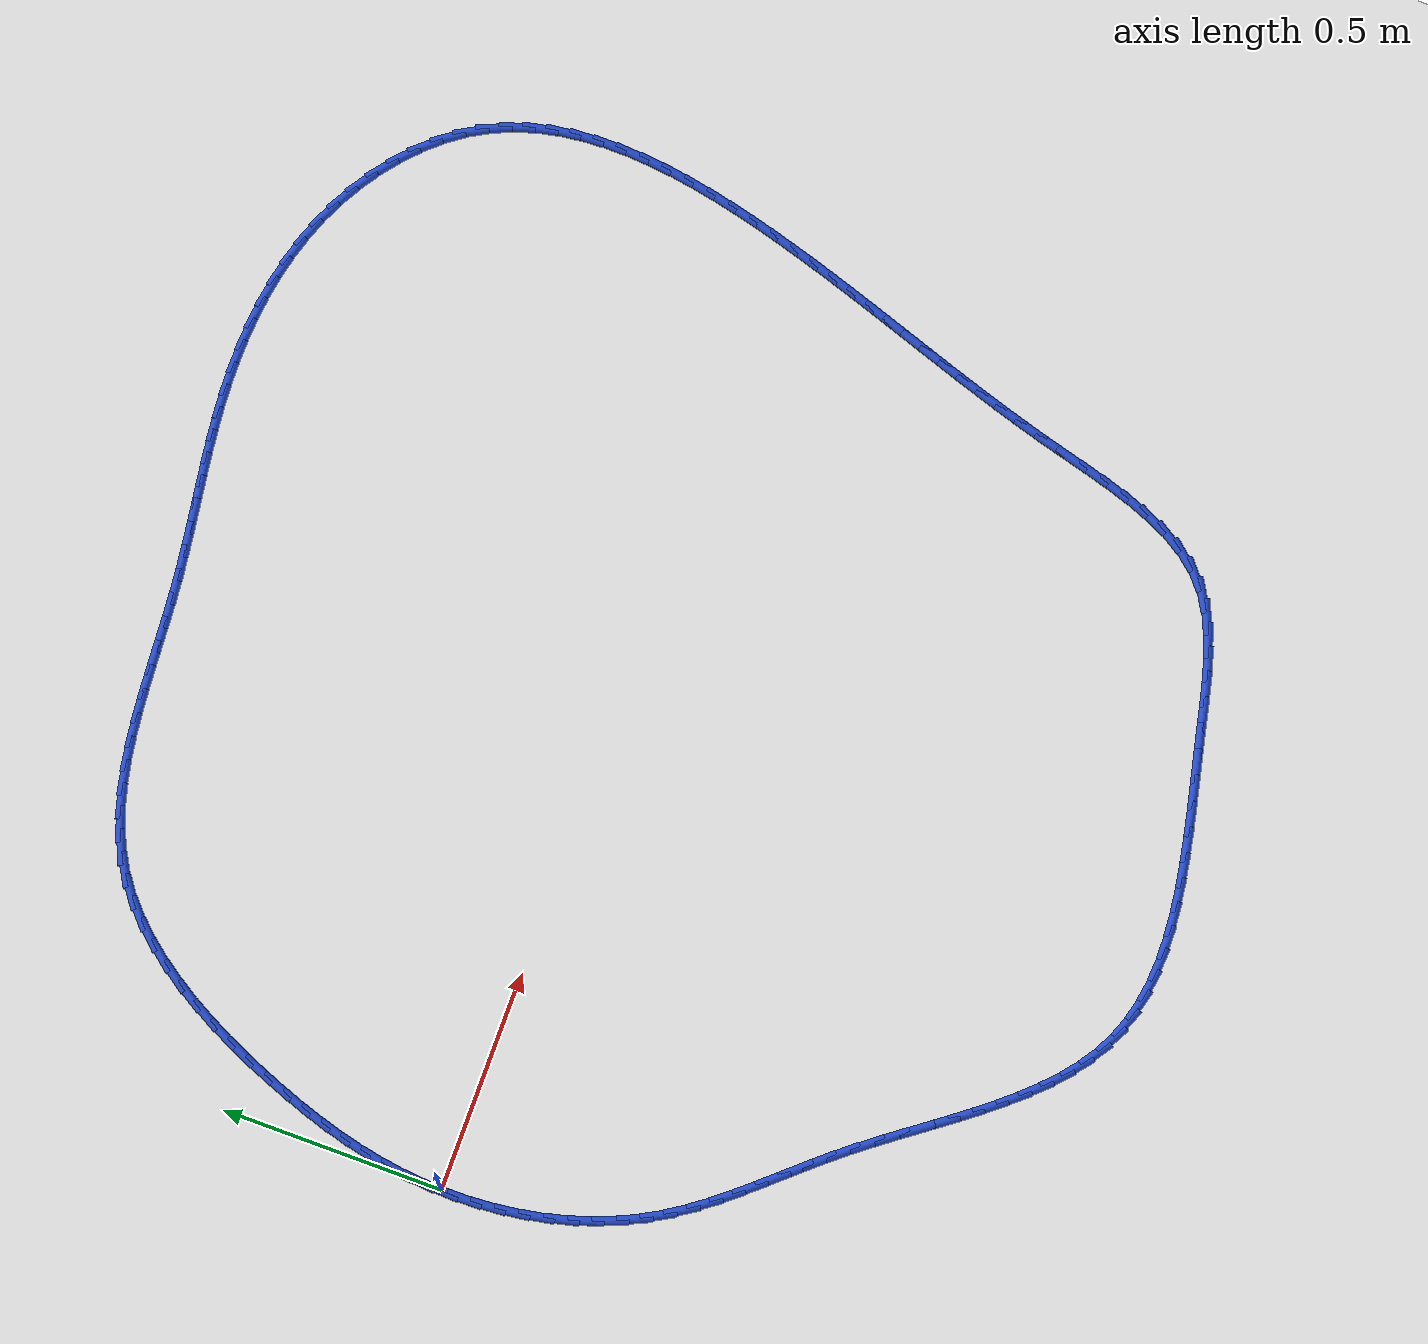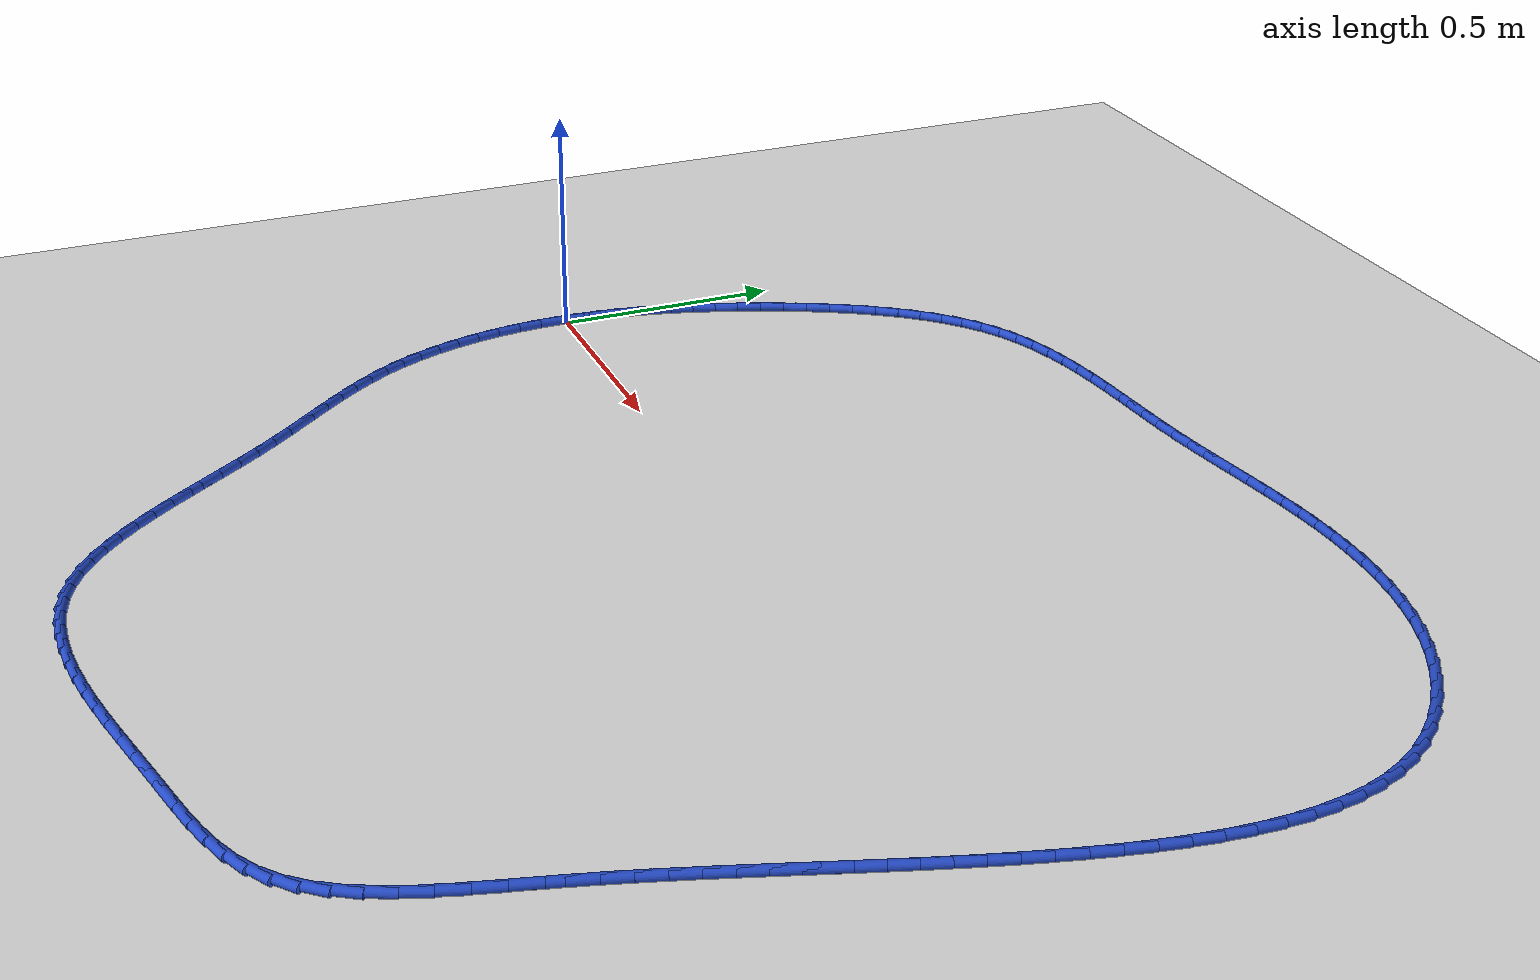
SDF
<sdf version="1.6">
 <world name="default">
  <light name="sun" type="directional">
   <pose>0 0 10 0 -0 0</pose>
   <diffuse>0.8 0.8 0.8 1</diffuse>
   <specular>0.2 0.2 0.2 1</specular>
   <attenuation>
    <range>1000</range>
    <constant>0.9</constant>
    <linear>0.01</linear>
    <quadratic>0.001</quadratic>
   </attenuation>
   <direction>-0.5 0.1 -0.9</direction>
  </light>
  <model name="ground_plane">
   <static>1</static>
   <link name="link">
    <collision name="collision">
     <geometry><plane><normal>0 0 1</normal><size>100 100</size></plane></geometry>
     <surface><friction><ode><mu>100</mu><mu2>50</mu2></ode></friction></surface>
    </collision>
    <visual name="visual">
     <cast_shadows>0</cast_shadows>
     <geometry><plane><normal>0 0 1</normal><size>100 100</size></plane></geometry>
     <material>
      <script><uri>file://media/materials/scripts/gazebo.material</uri><name>Gazebo/WhiteGlow</name></script>
     </material>
    </visual>
   </link>
  </model>
  <gravity>0 0 -9.8</gravity>
  <magnetic_field>6e-06 2.3e-05 -4.2e-05</magnetic_field>
  <atmosphere type="adiabatic"/>
  <physics name="default_physics" default="0" type="ode">
   <max_step_size>0.001</max_step_size>
   <real_time_factor>1</real_time_factor>
   <real_time_update_rate>1000</real_time_update_rate>
  </physics>
  <scene><ambient>0.4 0.4 0.4 1</ambient><background>0.7 0.7 0.7 1</background><shadows>1</shadows></scene>
  <spherical_coordinates>
   <surface_model>EARTH_WGS84</surface_model>
   <latitude_deg>0</latitude_deg>
   <longitude_deg>0</longitude_deg>
   <elevation>0</elevation>
   <heading_deg>0</heading_deg>
  </spherical_coordinates>
  <model name="line">
   <link name="link_0">
    <pose>4.85722573273506e-17 -1.5265566588595902e-16 0.01 0 1.57 1.5208682313684743</pose>
    <collision name="collision">
     <geometry><cylinder><radius>0.01</radius><length>0.08</length></cylinder></geometry>
    </collision>
    <visual name="visual">
     <material>
      <script><name>Gazebo/Blue</name><uri>file://media/materials/scripts/gazebo.material</uri></script>
     </material>
     <geometry><cylinder><radius>0.01</radius><length>0.08</length></cylinder></geometry>
    </visual>
   </link>
   <link name="link_1">
    <pose>0.0026078376806821296 0.05218845914660143 0.01 0 1.57 1.467295530697326</pose>
    <collision name="collision">
     <geometry><cylinder><radius>0.01</radius><length>0.08</length></cylinder></geometry>
    </collision>
    <visual name="visual">
     <material>
      <script><name>Gazebo/Blue</name><uri>file://media/materials/scripts/gazebo.material</uri></script>
     </material>
     <geometry><cylinder><radius>0.01</radius><length>0.08</length></cylinder></geometry>
    </visual>
   </link>
   <link name="link_2">
    <pose>0.007972753262551802 0.10383777027473558 0.01 0 1.57 1.4166332415653873</pose>
    <collision name="collision">
     <geometry><cylinder><radius>0.01</radius><length>0.08</length></cylinder></geometry>
    </collision>
    <visual name="visual">
     <material>
      <script><name>Gazebo/Blue</name><uri>file://media/materials/scripts/gazebo.material</uri></script>
     </material>
     <geometry><cylinder><radius>0.01</radius><length>0.08</length></cylinder></geometry>
    </visual>
   </link>
   <link name="link_3">
    <pose>0.01592972599528196 0.1550422256092562 0.01 0 1.57 1.3693722985429952</pose>
    <collision name="collision">
     <geometry><cylinder><radius>0.01</radius><length>0.08</length></cylinder></geometry>
    </collision>
    <visual name="visual">
     <material>
      <script><name>Gazebo/Blue</name><uri>file://media/materials/scripts/gazebo.material</uri></script>
     </material>
     <geometry><cylinder><radius>0.01</radius><length>0.08</length></cylinder></geometry>
    </visual>
   </link>
   <link name="link_4">
    <pose>0.02631373512854548 0.2058961173750172 0.01 0 1.57 1.3258805427027616</pose>
    <collision name="collision">
     <geometry><cylinder><radius>0.01</radius><length>0.08</length></cylinder></geometry>
    </collision>
    <visual name="visual">
     <material>
      <script><name>Gazebo/Blue</name><uri>file://media/materials/scripts/gazebo.material</uri></script>
     </material>
     <geometry><cylinder><radius>0.01</radius><length>0.08</length></cylinder></geometry>
    </visual>
   </link>
   <link name="link_5">
    <pose>0.038959759912015265 0.25649373779687257 0.01 0 1.57 1.286406184170897</pose>
    <collision name="collision">
     <geometry><cylinder><radius>0.01</radius><length>0.08</length></cylinder></geometry>
    </collision>
    <visual name="visual">
     <material>
      <script><name>Gazebo/Blue</name><uri>file://media/materials/scripts/gazebo.material</uri></script>
     </material>
     <geometry><cylinder><radius>0.01</radius><length>0.08</length></cylinder></geometry>
    </visual>
   </link>
   <link name="link_6">
    <pose>0.053702779595364195 0.3069293790996761 0.01 0 1.57 1.251089965797741</pose>
    <collision name="collision">
     <geometry><cylinder><radius>0.01</radius><length>0.08</length></cylinder></geometry>
    </collision>
    <visual name="visual">
     <material>
      <script><name>Gazebo/Blue</name><uri>file://media/materials/scripts/gazebo.material</uri></script>
     </material>
     <geometry><cylinder><radius>0.01</radius><length>0.08</length></cylinder></geometry>
    </visual>
   </link>
   <link name="link_7">
    <pose>0.07037777342826515 0.35729733350828197 0.01 0 1.57 1.2199823960051726</pose>
    <collision name="collision">
     <geometry><cylinder><radius>0.01</radius><length>0.08</length></cylinder></geometry>
    </collision>
    <visual name="visual">
     <material>
      <script><name>Gazebo/Blue</name><uri>file://media/materials/scripts/gazebo.material</uri></script>
     </material>
     <geometry><cylinder><radius>0.01</radius><length>0.08</length></cylinder></geometry>
    </visual>
   </link>
   <link name="link_8">
    <pose>0.08881972066039102 0.4076918932475438 0.01 0 1.57 1.1929046623063255</pose>
    <collision name="collision">
     <geometry><cylinder><radius>0.01</radius><length>0.08</length></cylinder></geometry>
    </collision>
    <visual name="visual">
     <material>
      <script><name>Gazebo/Blue</name><uri>file://media/materials/scripts/gazebo.material</uri></script>
     </material>
     <geometry><cylinder><radius>0.01</radius><length>0.08</length></cylinder></geometry>
    </visual>
   </link>
   <link name="link_9">
    <pose>0.10886869613879971 0.4581968952906872 0.01 0 1.57 1.1657548896957421</pose>
    <collision name="collision">
     <geometry><cylinder><radius>0.01</radius><length>0.08</length></cylinder></geometry>
    </collision>
    <visual name="visual">
     <material>
      <script><name>Gazebo/Blue</name><uri>file://media/materials/scripts/gazebo.material</uri></script>
     </material>
     <geometry><cylinder><radius>0.01</radius><length>0.08</length></cylinder></geometry>
    </visual>
   </link>
   <link name="link_10">
    <pose>0.1304930740329941 0.5086329294195757 0.01 0 1.57 1.1339866158312886</pose>
    <collision name="collision">
     <geometry><cylinder><radius>0.01</radius><length>0.08</length></cylinder></geometry>
    </collision>
    <visual name="visual">
     <material>
      <script><name>Gazebo/Blue</name><uri>file://media/materials/scripts/gazebo.material</uri></script>
     </material>
     <geometry><cylinder><radius>0.01</radius><length>0.08</length></cylinder></geometry>
    </visual>
   </link>
   <link name="link_11">
    <pose>0.15379601572929497 0.558544026229456 0.01 0 1.57 1.0968578496795356</pose>
    <collision name="collision">
     <geometry><cylinder><radius>0.01</radius><length>0.08</length></cylinder></geometry>
    </collision>
    <visual name="visual">
     <material>
      <script><name>Gazebo/Blue</name><uri>file://media/materials/scripts/gazebo.material</uri></script>
     </material>
     <geometry><cylinder><radius>0.01</radius><length>0.08</length></cylinder></geometry>
    </visual>
   </link>
   <link name="link_12">
    <pose>0.1788870767802631 0.6074610966336335 0.01 0 1.57 1.053682933256067</pose>
    <collision name="collision">
     <geometry><cylinder><radius>0.01</radius><length>0.08</length></cylinder></geometry>
    </collision>
    <visual name="visual">
     <material>
      <script><name>Gazebo/Blue</name><uri>file://media/materials/scripts/gazebo.material</uri></script>
     </material>
     <geometry><cylinder><radius>0.01</radius><length>0.08</length></cylinder></geometry>
    </visual>
   </link>
   <link name="link_13">
    <pose>0.20587581273845934 0.6549150515454136 0.01 0 1.57 1.003635997291884</pose>
    <collision name="collision">
     <geometry><cylinder><radius>0.01</radius><length>0.08</length></cylinder></geometry>
    </collision>
    <visual name="visual">
     <material>
      <script><name>Gazebo/Blue</name><uri>file://media/materials/scripts/gazebo.material</uri></script>
     </material>
     <geometry><cylinder><radius>0.01</radius><length>0.08</length></cylinder></geometry>
    </visual>
   </link>
   <link name="link_14">
    <pose>0.2348717791564443 0.7004368018781018 0.01 0 1.57 0.9457656126940531</pose>
    <collision name="collision">
     <geometry><cylinder><radius>0.01</radius><length>0.08</length></cylinder></geometry>
    </collision>
    <visual name="visual">
     <material>
      <script><name>Gazebo/Blue</name><uri>file://media/materials/scripts/gazebo.material</uri></script>
     </material>
     <geometry><cylinder><radius>0.01</radius><length>0.08</length></cylinder></geometry>
    </visual>
   </link>
   <link name="link_15">
    <pose>0.265984531586779 0.7435572585450035 0.01 0 1.57 0.879036527268992</pose>
    <collision name="collision">
     <geometry><cylinder><radius>0.01</radius><length>0.08</length></cylinder></geometry>
    </collision>
    <visual name="visual">
     <material>
      <script><name>Gazebo/Blue</name><uri>file://media/materials/scripts/gazebo.material</uri></script>
     </material>
     <geometry><cylinder><radius>0.01</radius><length>0.08</length></cylinder></geometry>
    </visual>
   </link>
   <link name="link_16">
    <pose>0.299323625582024 0.7838073324594245 0.01 0 1.57 0.8024193321833599</pose>
    <collision name="collision">
     <geometry><cylinder><radius>0.01</radius><length>0.08</length></cylinder></geometry>
    </collision>
    <visual name="visual">
     <material>
      <script><name>Gazebo/Blue</name><uri>file://media/materials/scripts/gazebo.material</uri></script>
     </material>
     <geometry><cylinder><radius>0.01</radius><length>0.08</length></cylinder></geometry>
    </visual>
   </link>
   <link name="link_17">
    <pose>0.3349986166947402 0.8207179345346696 0.01 0 1.57 0.7150534925548987</pose>
    <collision name="collision">
     <geometry><cylinder><radius>0.01</radius><length>0.08</length></cylinder></geometry>
    </collision>
    <visual name="visual">
     <material>
      <script><name>Gazebo/Blue</name><uri>file://media/materials/scripts/gazebo.material</uri></script>
     </material>
     <geometry><cylinder><radius>0.01</radius><length>0.08</length></cylinder></geometry>
    </visual>
   </link>
   <link name="link_18">
    <pose>0.37311906047748816 0.8538199756840446 0.01 0 1.57 0.6165033880333615</pose>
    <collision name="collision">
     <geometry><cylinder><radius>0.01</radius><length>0.08</length></cylinder></geometry>
    </collision>
    <visual name="visual">
     <material>
      <script><name>Gazebo/Blue</name><uri>file://media/materials/scripts/gazebo.material</uri></script>
     </material>
     <geometry><cylinder><radius>0.01</radius><length>0.08</length></cylinder></geometry>
    </visual>
   </link>
   <link name="link_19">
    <pose>0.41379451248282906 0.8826443668208552 0.01 0 1.57 0.5097273781721162</pose>
    <collision name="collision">
     <geometry><cylinder><radius>0.01</radius><length>0.08</length></cylinder></geometry>
    </collision>
    <visual name="visual">
     <material>
      <script><name>Gazebo/Blue</name><uri>file://media/materials/scripts/gazebo.material</uri></script>
     </material>
     <geometry><cylinder><radius>0.01</radius><length>0.08</length></cylinder></geometry>
    </visual>
   </link>
   <link name="link_20">
    <pose>0.4570848592107376 0.9068437074329452 0.01 0 1.57 0.4100828563643528</pose>
    <collision name="collision">
     <geometry><cylinder><radius>0.01</radius><length>0.08</length></cylinder></geometry>
    </collision>
    <visual name="visual">
     <material>
      <script><name>Gazebo/Blue</name><uri>file://media/materials/scripts/gazebo.material</uri></script>
     </material>
     <geometry><cylinder><radius>0.01</radius><length>0.08</length></cylinder></geometry>
    </visual>
   </link>
   <link name="link_21">
    <pose>0.5027880837160641 0.9267122572622769 0.01 0 1.57 0.32363220275786153</pose>
    <collision name="collision">
     <geometry><cylinder><radius>0.01</radius><length>0.08</length></cylinder></geometry>
    </collision>
    <visual name="visual">
     <material>
      <script><name>Gazebo/Blue</name><uri>file://media/materials/scripts/gazebo.material</uri></script>
     </material>
     <geometry><cylinder><radius>0.01</radius><length>0.08</length></cylinder></geometry>
    </visual>
   </link>
   <link name="link_22">
    <pose>0.550616156344528 0.9427550061417145 0.01 0 1.57 0.25076629282586843</pose>
    <collision name="collision">
     <geometry><cylinder><radius>0.01</radius><length>0.08</length></cylinder></geometry>
    </collision>
    <visual name="visual">
     <material>
      <script><name>Gazebo/Blue</name><uri>file://media/materials/scripts/gazebo.material</uri></script>
     </material>
     <geometry><cylinder><radius>0.01</radius><length>0.08</length></cylinder></geometry>
    </visual>
   </link>
   <link name="link_23">
    <pose>0.6002809964129442 0.9554770689243158 0.01 0 1.57 0.191075220446858</pose>
    <collision name="collision">
     <geometry><cylinder><radius>0.01</radius><length>0.08</length></cylinder></geometry>
    </collision>
    <visual name="visual">
     <material>
      <script><name>Gazebo/Blue</name><uri>file://media/materials/scripts/gazebo.material</uri></script>
     </material>
     <geometry><cylinder><radius>0.01</radius><length>0.08</length></cylinder></geometry>
    </visual>
   </link>
   <link name="link_24">
    <pose>0.6514945232381278 0.9653835604631394 0.01 0 1.57 0.14375910972457667</pose>
    <collision name="collision">
     <geometry><cylinder><radius>0.01</radius><length>0.08</length></cylinder></geometry>
    </collision>
    <visual name="visual">
     <material>
      <script><name>Gazebo/Blue</name><uri>file://media/materials/scripts/gazebo.material</uri></script>
     </material>
     <geometry><cylinder><radius>0.01</radius><length>0.08</length></cylinder></geometry>
    </visual>
   </link>
   <link name="link_25">
    <pose>0.7039686561368935 0.9729795956112431 0.01 0 1.57 0.10792430526535217</pose>
    <collision name="collision">
     <geometry><cylinder><radius>0.01</radius><length>0.08</length></cylinder></geometry>
    </collision>
    <visual name="visual">
     <material>
      <script><name>Gazebo/Blue</name><uri>file://media/materials/scripts/gazebo.material</uri></script>
     </material>
     <geometry><cylinder><radius>0.01</radius><length>0.08</length></cylinder></geometry>
    </visual>
   </link>
   <link name="link_26">
    <pose>0.7574153144260567 0.9787702892216857 0.01 0 1.57 0.0827658863774594</pose>
    <collision name="collision">
     <geometry><cylinder><radius>0.01</radius><length>0.08</length></cylinder></geometry>
    </collision>
    <visual name="visual">
     <material>
      <script><name>Gazebo/Blue</name><uri>file://media/materials/scripts/gazebo.material</uri></script>
     </material>
     <geometry><cylinder><radius>0.01</radius><length>0.08</length></cylinder></geometry>
    </visual>
   </link>
   <link name="link_27">
    <pose>0.8115464174224319 0.9832607561475252 0.01 0 1.57 0.06766705732779447</pose>
    <collision name="collision">
     <geometry><cylinder><radius>0.01</radius><length>0.08</length></cylinder></geometry>
    </collision>
    <visual name="visual">
     <material>
      <script><name>Gazebo/Blue</name><uri>file://media/materials/scripts/gazebo.material</uri></script>
     </material>
     <geometry><cylinder><radius>0.01</radius><length>0.08</length></cylinder></geometry>
    </visual>
   </link>
   <link name="link_28">
    <pose>0.8660738844428348 0.9869561112418198 0.01 0 1.57 0.06224786152688509</pose>
    <collision name="collision">
     <geometry><cylinder><radius>0.01</radius><length>0.08</length></cylinder></geometry>
    </collision>
    <visual name="visual">
     <material>
      <script><name>Gazebo/Blue</name><uri>file://media/materials/scripts/gazebo.material</uri></script>
     </material>
     <geometry><cylinder><radius>0.01</radius><length>0.08</length></cylinder></geometry>
    </visual>
   </link>
   <link name="link_29">
    <pose>0.92070963480408 0.9903614693576281 0.01 0 1.57 0.06638678600840407</pose>
    <collision name="collision">
     <geometry><cylinder><radius>0.01</radius><length>0.08</length></cylinder></geometry>
    </collision>
    <visual name="visual">
     <material>
      <script><name>Gazebo/Blue</name><uri>file://media/materials/scripts/gazebo.material</uri></script>
     </material>
     <geometry><cylinder><radius>0.01</radius><length>0.08</length></cylinder></geometry>
    </visual>
   </link>
   <link name="link_30">
    <pose>0.9751655878229826 0.9939819453480081 0.01 0 1.57 0.08022867136884439</pose>
    <collision name="collision">
     <geometry><cylinder><radius>0.01</radius><length>0.08</length></cylinder></geometry>
    </collision>
    <visual name="visual">
     <material>
      <script><name>Gazebo/Blue</name><uri>file://media/materials/scripts/gazebo.material</uri></script>
     </material>
     <geometry><cylinder><radius>0.01</radius><length>0.08</length></cylinder></geometry>
    </visual>
   </link>
   <link name="link_31">
    <pose>1.0291536628163571 0.998322654066018 0.01 0 1.57 0.10244471837668626</pose>
    <collision name="collision">
     <geometry><cylinder><radius>0.01</radius><length>0.08</length></cylinder></geometry>
    </collision>
    <visual name="visual">
     <material>
      <script><name>Gazebo/Blue</name><uri>file://media/materials/scripts/gazebo.material</uri></script>
     </material>
     <geometry><cylinder><radius>0.01</radius><length>0.08</length></cylinder></geometry>
    </visual>
   </link>
   <link name="link_32">
    <pose>1.0824295440069132 1.0037996603782384 0.01 0 1.57 0.12221266401720902</pose>
    <collision name="collision">
     <geometry><cylinder><radius>0.01</radius><length>0.08</length></cylinder></geometry>
    </collision>
    <visual name="visual">
     <material>
      <script><name>Gazebo/Blue</name><uri>file://media/materials/scripts/gazebo.material</uri></script>
     </material>
     <geometry><cylinder><radius>0.01</radius><length>0.08</length></cylinder></geometry>
    </visual>
   </link>
   <link name="link_33">
    <pose>1.135028515628162 1.0102601172188883 0.01 0 1.57 0.13490801925859391</pose>
    <collision name="collision">
     <geometry><cylinder><radius>0.01</radius><length>0.08</length></cylinder></geometry>
    </collision>
    <visual name="visual">
     <material>
      <script><name>Gazebo/Blue</name><uri>file://media/materials/scripts/gazebo.material</uri></script>
     </material>
     <geometry><cylinder><radius>0.01</radius><length>0.08</length></cylinder></geometry>
    </visual>
   </link>
   <link name="link_34">
    <pose>1.1870958664510638 1.0173273474379692 0.01 0 1.57 0.14026115526694666</pose>
    <collision name="collision">
     <geometry><cylinder><radius>0.01</radius><length>0.08</length></cylinder></geometry>
    </collision>
    <visual name="visual">
     <material>
      <script><name>Gazebo/Blue</name><uri>file://media/materials/scripts/gazebo.material</uri></script>
     </material>
     <geometry><cylinder><radius>0.01</radius><length>0.08</length></cylinder></geometry>
    </visual>
   </link>
   <link name="link_35">
    <pose>1.2387771490583237 1.0246241370984779 0.01 0 1.57 0.13809345208725277</pose>
    <collision name="collision">
     <geometry><cylinder><radius>0.01</radius><length>0.08</length></cylinder></geometry>
    </collision>
    <visual name="visual">
     <material>
      <script><name>Gazebo/Blue</name><uri>file://media/materials/scripts/gazebo.material</uri></script>
     </material>
     <geometry><cylinder><radius>0.01</radius><length>0.08</length></cylinder></geometry>
    </visual>
   </link>
   <link name="link_36">
    <pose>1.2902179160326488 1.031773272263413 0.01 0 1.57 0.12830410355506472</pose>
    <collision name="collision">
     <geometry><cylinder><radius>0.01</radius><length>0.08</length></cylinder></geometry>
    </collision>
    <visual name="visual">
     <material>
      <script><name>Gazebo/Blue</name><uri>file://media/materials/scripts/gazebo.material</uri></script>
     </material>
     <geometry><cylinder><radius>0.01</radius><length>0.08</length></cylinder></geometry>
    </visual>
   </link>
   <link name="link_37">
    <pose>1.3415637199567456 1.0383975389957725 0.01 0 1.57 0.11087773809146687</pose>
    <collision name="collision">
     <geometry><cylinder><radius>0.01</radius><length>0.08</length></cylinder></geometry>
    </collision>
    <visual name="visual">
     <material>
      <script><name>Gazebo/Blue</name><uri>file://media/materials/scripts/gazebo.material</uri></script>
     </material>
     <geometry><cylinder><radius>0.01</radius><length>0.08</length></cylinder></geometry>
    </visual>
   </link>
   <link name="link_38">
    <pose>1.3929601134133198 1.0441197233585546 0.01 0 1.57 0.08590301132738641</pose>
    <collision name="collision">
     <geometry><cylinder><radius>0.01</radius><length>0.08</length></cylinder></geometry>
    </collision>
    <visual name="visual">
     <material>
      <script><name>Gazebo/Blue</name><uri>file://media/materials/scripts/gazebo.material</uri></script>
     </material>
     <geometry><cylinder><radius>0.01</radius><length>0.08</length></cylinder></geometry>
    </visual>
   </link>
   <link name="link_39">
    <pose>1.4445526489850795 1.0485626114147577 0.01 0 1.57 0.053619003104559165</pose>
    <collision name="collision">
     <geometry><cylinder><radius>0.01</radius><length>0.08</length></cylinder></geometry>
    </collision>
    <visual name="visual">
     <material>
      <script><name>Gazebo/Blue</name><uri>file://media/materials/scripts/gazebo.material</uri></script>
     </material>
     <geometry><cylinder><radius>0.01</radius><length>0.08</length></cylinder></geometry>
    </visual>
   </link>
   <link name="link_40">
    <pose>1.4964848915391884 1.0513498380914954 0.01 0 1.57 0.0154529390688499</pose>
    <collision name="collision">
     <geometry><cylinder><radius>0.01</radius><length>0.08</length></cylinder></geometry>
    </collision>
    <visual name="visual">
     <material>
      <script><name>Gazebo/Blue</name><uri>file://media/materials/scripts/gazebo.material</uri></script>
     </material>
     <geometry><cylinder><radius>0.01</radius><length>0.08</length></cylinder></geometry>
    </visual>
   </link>
   <link name="link_41">
    <pose>1.5487764808535205 1.0521579611608056 0.01 0 1.57 -0.02688644155528152</pose>
    <collision name="collision">
     <geometry><cylinder><radius>0.01</radius><length>0.08</length></cylinder></geometry>
    </collision>
    <visual name="visual">
     <material>
      <script><name>Gazebo/Blue</name><uri>file://media/materials/scripts/gazebo.material</uri></script>
     </material>
     <geometry><cylinder><radius>0.01</radius><length>0.08</length></cylinder></geometry>
    </visual>
   </link>
   <link name="link_42">
    <pose>1.601252243010109 1.0507467345826207 0.01 0 1.57 -0.07350367243640493</pose>
    <collision name="collision">
     <geometry><cylinder><radius>0.01</radius><length>0.08</length></cylinder></geometry>
    </collision>
    <visual name="visual">
     <material>
      <script><name>Gazebo/Blue</name><uri>file://media/materials/scripts/gazebo.material</uri></script>
     </material>
     <geometry><cylinder><radius>0.01</radius><length>0.08</length></cylinder></geometry>
    </visual>
   </link>
   <link name="link_43">
    <pose>1.6537199227603057 1.0468832069867453 0.01 0 1.57 -0.1246443785448311</pose>
    <collision name="collision">
     <geometry><cylinder><radius>0.01</radius><length>0.08</length></cylinder></geometry>
    </collision>
    <visual name="visual">
     <material>
      <script><name>Gazebo/Blue</name><uri>file://media/materials/scripts/gazebo.material</uri></script>
     </material>
     <geometry><cylinder><radius>0.01</radius><length>0.08</length></cylinder></geometry>
    </visual>
   </link>
   <link name="link_44">
    <pose>1.7059872648554595 1.0403344270029815 0.01 0 1.57 -0.18051047314980015</pose>
    <collision name="collision">
     <geometry><cylinder><radius>0.01</radius><length>0.08</length></cylinder></geometry>
    </collision>
    <visual name="visual">
     <material>
      <script><name>Gazebo/Blue</name><uri>file://media/materials/scripts/gazebo.material</uri></script>
     </material>
     <geometry><cylinder><radius>0.01</radius><length>0.08</length></cylinder></geometry>
    </visual>
   </link>
   <link name="link_45">
    <pose>1.757862014046921 1.0308674432611329 0.01 0 1.57 -0.24122556278892943</pose>
    <collision name="collision">
     <geometry><cylinder><radius>0.01</radius><length>0.08</length></cylinder></geometry>
    </collision>
    <visual name="visual">
     <material>
      <script><name>Gazebo/Blue</name><uri>file://media/materials/scripts/gazebo.material</uri></script>
     </material>
     <geometry><cylinder><radius>0.01</radius><length>0.08</length></cylinder></geometry>
    </visual>
   </link>
   <link name="link_46">
    <pose>1.8091519150860405 1.0182493043910021 0.01 0 1.57 -0.3067937374642632</pose>
    <collision name="collision">
     <geometry><cylinder><radius>0.01</radius><length>0.08</length></cylinder></geometry>
    </collision>
    <visual name="visual">
     <material>
      <script><name>Gazebo/Blue</name><uri>file://media/materials/scripts/gazebo.material</uri></script>
     </material>
     <geometry><cylinder><radius>0.01</radius><length>0.08</length></cylinder></geometry>
    </visual>
   </link>
   <link name="link_47">
    <pose>1.8596647127241663 1.0022470590223929 0.01 0 1.57 -0.37705512136661634</pose>
    <collision name="collision">
     <geometry><cylinder><radius>0.01</radius><length>0.08</length></cylinder></geometry>
    </collision>
    <visual name="visual">
     <material>
      <script><name>Gazebo/Blue</name><uri>file://media/materials/scripts/gazebo.material</uri></script>
     </material>
     <geometry><cylinder><radius>0.01</radius><length>0.08</length></cylinder></geometry>
    </visual>
   </link>
   <link name="link_48">
    <pose>1.90920815171265 0.9826277557851075 0.01 0 1.57 -0.45120357299616404</pose>
    <collision name="collision">
     <geometry><cylinder><radius>0.01</radius><length>0.08</length></cylinder></geometry>
    </collision>
    <visual name="visual">
     <material>
      <script><name>Gazebo/Blue</name><uri>file://media/materials/scripts/gazebo.material</uri></script>
     </material>
     <geometry><cylinder><radius>0.01</radius><length>0.08</length></cylinder></geometry>
    </visual>
   </link>
   <link name="link_49">
    <pose>1.9575530177345846 0.9592027176161821 0.01 0 1.57 -0.5264947639277594</pose>
    <collision name="collision">
     <geometry><cylinder><radius>0.01</radius><length>0.08</length></cylinder></geometry>
    </collision>
    <visual name="visual">
     <material>
      <script><name>Gazebo/Blue</name><uri>file://media/materials/scripts/gazebo.material</uri></script>
     </material>
     <geometry><cylinder><radius>0.01</radius><length>0.08</length></cylinder></geometry>
    </visual>
   </link>
   <link name="link_50">
    <pose>2.004226227486883 0.9320754049693192 0.01 0 1.57 -0.6032399173432121</pose>
    <collision name="collision">
     <geometry><cylinder><radius>0.01</radius><length>0.08</length></cylinder></geometry>
    </collision>
    <visual name="visual">
     <material>
      <script><name>Gazebo/Blue</name><uri>file://media/materials/scripts/gazebo.material</uri></script>
     </material>
     <geometry><cylinder><radius>0.01</radius><length>0.08</length></cylinder></geometry>
    </visual>
   </link>
   <link name="link_51">
    <pose>2.048655886118196 0.9014676474306744 0.01 0 1.57 -0.683108060337162</pose>
    <collision name="collision">
     <geometry><cylinder><radius>0.01</radius><length>0.08</length></cylinder></geometry>
    </collision>
    <visual name="visual">
     <material>
      <script><name>Gazebo/Blue</name><uri>file://media/materials/scripts/gazebo.material</uri></script>
     </material>
     <geometry><cylinder><radius>0.01</radius><length>0.08</length></cylinder></geometry>
    </visual>
   </link>
   <link name="link_52">
    <pose>2.0902698180341455 0.8676016108963779 0.01 0 1.57 -0.7677783703944429</pose>
    <collision name="collision">
     <geometry><cylinder><radius>0.01</radius><length>0.08</length></cylinder></geometry>
    </collision>
    <visual name="visual">
     <material>
      <script><name>Gazebo/Blue</name><uri>file://media/materials/scripts/gazebo.material</uri></script>
     </material>
     <geometry><cylinder><radius>0.01</radius><length>0.08</length></cylinder></geometry>
    </visual>
   </link>
   <link name="link_53">
    <pose>2.128495847640349 0.8306994612625599 0.01 0 1.57 -0.8589338092545327</pose>
    <collision name="collision">
     <geometry><cylinder><radius>0.01</radius><length>0.08</length></cylinder></geometry>
    </collision>
    <visual name="visual">
     <material>
      <script><name>Gazebo/Blue</name><uri>file://media/materials/scripts/gazebo.material</uri></script>
     </material>
     <geometry><cylinder><radius>0.01</radius><length>0.08</length></cylinder></geometry>
    </visual>
   </link>
   <link name="link_54">
    <pose>2.162761799342427 0.7909833644253507 0.01 0 1.57 -0.9581980458995797</pose>
    <collision name="collision">
     <geometry><cylinder><radius>0.01</radius><length>0.08</length></cylinder></geometry>
    </collision>
    <visual name="visual">
     <material>
      <script><name>Gazebo/Blue</name><uri>file://media/materials/scripts/gazebo.material</uri></script>
     </material>
     <geometry><cylinder><radius>0.01</radius><length>0.08</length></cylinder></geometry>
    </visual>
   </link>
   <link name="link_55">
    <pose>2.1924954975459996 0.7486754862808791 0.01 0 1.57 -1.0665975625031598</pose>
    <collision name="collision">
     <geometry><cylinder><radius>0.01</radius><length>0.08</length></cylinder></geometry>
    </collision>
    <visual name="visual">
     <material>
      <script><name>Gazebo/Blue</name><uri>file://media/materials/scripts/gazebo.material</uri></script>
     </material>
     <geometry><cylinder><radius>0.01</radius><length>0.08</length></cylinder></geometry>
    </visual>
   </link>
   <link name="link_56">
    <pose>2.217146666160847 0.7039987080563526 0.01 0 1.57 -1.1764557857700109</pose>
    <collision name="collision">
     <geometry><cylinder><radius>0.01</radius><length>0.08</length></cylinder></geometry>
    </collision>
    <visual name="visual">
     <material>
      <script><name>Gazebo/Blue</name><uri>file://media/materials/scripts/gazebo.material</uri></script>
     </material>
     <geometry><cylinder><radius>0.01</radius><length>0.08</length></cylinder></geometry>
    </visual>
   </link>
   <link name="link_57">
    <pose>2.2366251550820673 0.657190940653333 0.01 0 1.57 -1.2784571123407862</pose>
    <collision name="collision">
     <geometry><cylinder><radius>0.01</radius><length>0.08</length></cylinder></geometry>
    </collision>
    <visual name="visual">
     <material>
      <script><name>Gazebo/Blue</name><uri>file://media/materials/scripts/gazebo.material</uri></script>
     </material>
     <geometry><cylinder><radius>0.01</radius><length>0.08</length></cylinder></geometry>
    </visual>
   </link>
   <link name="link_58">
    <pose>2.2512779660050435 0.6085043742130103 0.01 0 1.57 -1.3709382837595616</pose>
    <collision name="collision">
     <geometry><cylinder><radius>0.01</radius><length>0.08</length></cylinder></geometry>
    </collision>
    <visual name="visual">
     <material>
      <script><name>Gazebo/Blue</name><uri>file://media/materials/scripts/gazebo.material</uri></script>
     </material>
     <geometry><cylinder><radius>0.01</radius><length>0.08</length></cylinder></geometry>
    </visual>
   </link>
   <link name="link_59">
    <pose>2.2614694015131507 0.5581917639972597 0.01 0 1.57 -1.453426743368012</pose>
    <collision name="collision">
     <geometry><cylinder><radius>0.01</radius><length>0.08</length></cylinder></geometry>
    </collision>
    <visual name="visual">
     <material>
      <script><name>Gazebo/Blue</name><uri>file://media/materials/scripts/gazebo.material</uri></script>
     </material>
     <geometry><cylinder><radius>0.01</radius><length>0.08</length></cylinder></geometry>
    </visual>
   </link>
   <link name="link_60">
    <pose>2.267563764189766 0.5065058652679577 0.01 0 1.57 -1.5261044245211823</pose>
    <collision name="collision">
     <geometry><cylinder><radius>0.01</radius><length>0.08</length></cylinder></geometry>
    </collision>
    <visual name="visual">
     <material>
      <script><name>Gazebo/Blue</name><uri>file://media/materials/scripts/gazebo.material</uri></script>
     </material>
     <geometry><cylinder><radius>0.01</radius><length>0.08</length></cylinder></geometry>
    </visual>
   </link>
   <link name="link_61">
    <pose>2.2699253566182658 0.4536994332869794 0.01 0 1.57 1.55203951313978</pose>
    <collision name="collision">
     <geometry><cylinder><radius>0.01</radius><length>0.08</length></cylinder></geometry>
    </collision>
    <visual name="visual">
     <material>
      <script><name>Gazebo/Blue</name><uri>file://media/materials/scripts/gazebo.material</uri></script>
     </material>
     <geometry><cylinder><radius>0.01</radius><length>0.08</length></cylinder></geometry>
    </visual>
   </link>
   <link name="link_62">
    <pose>2.268918481382025 0.40002522331620144 0.01 0 1.57 1.4970475258395013</pose>
    <collision name="collision">
     <geometry><cylinder><radius>0.01</radius><length>0.08</length></cylinder></geometry>
    </collision>
    <visual name="visual">
     <material>
      <script><name>Gazebo/Blue</name><uri>file://media/materials/scripts/gazebo.material</uri></script>
     </material>
     <geometry><cylinder><radius>0.01</radius><length>0.08</length></cylinder></geometry>
    </visual>
   </link>
   <link name="link_63">
    <pose>2.2649074410644205 0.3457359906174987 0.01 0 1.57 1.4496952030478256</pose>
    <collision name="collision">
     <geometry><cylinder><radius>0.01</radius><length>0.08</length></cylinder></geometry>
    </collision>
    <visual name="visual">
     <material>
      <script><name>Gazebo/Blue</name><uri>file://media/materials/scripts/gazebo.material</uri></script>
     </material>
     <geometry><cylinder><radius>0.01</radius><length>0.08</length></cylinder></geometry>
    </visual>
   </link>
   <link name="link_64">
    <pose>2.258256538248828 0.29108449045274776 0.01 0 1.57 1.4092098937880944</pose>
    <collision name="collision">
     <geometry><cylinder><radius>0.01</radius><length>0.08</length></cylinder></geometry>
    </collision>
    <visual name="visual">
     <material>
      <script><name>Gazebo/Blue</name><uri>file://media/materials/scripts/gazebo.material</uri></script>
     </material>
     <geometry><cylinder><radius>0.01</radius><length>0.08</length></cylinder></geometry>
    </visual>
   </link>
   <link name="link_65">
    <pose>2.249330075518625 0.2363234780838242 0.01 0 1.57 1.3749123150973601</pose>
    <collision name="collision">
     <geometry><cylinder><radius>0.01</radius><length>0.08</length></cylinder></geometry>
    </collision>
    <visual name="visual">
     <material>
      <script><name>Gazebo/Blue</name><uri>file://media/materials/scripts/gazebo.material</uri></script>
     </material>
     <geometry><cylinder><radius>0.01</radius><length>0.08</length></cylinder></geometry>
    </visual>
   </link>
   <link name="link_66">
    <pose>2.238492355457186 0.18170570877260325 0.01 0 1.57 1.3462406789533357</pose>
    <collision name="collision">
     <geometry><cylinder><radius>0.01</radius><length>0.08</length></cylinder></geometry>
    </collision>
    <visual name="visual">
     <material>
      <script><name>Gazebo/Blue</name><uri>file://media/materials/scripts/gazebo.material</uri></script>
     </material>
     <geometry><cylinder><radius>0.01</radius><length>0.08</length></cylinder></geometry>
    </visual>
   </link>
   <link name="link_67">
    <pose>2.2261076806478886 0.12748393778096162 0.01 0 1.57 1.3227618830945307</pose>
    <collision name="collision">
     <geometry><cylinder><radius>0.01</radius><length>0.08</length></cylinder></geometry>
    </collision>
    <visual name="visual">
     <material>
      <script><name>Gazebo/Blue</name><uri>file://media/materials/scripts/gazebo.material</uri></script>
     </material>
     <geometry><cylinder><radius>0.01</radius><length>0.08</length></cylinder></geometry>
    </visual>
   </link>
   <link name="link_68">
    <pose>2.212540353674107 0.07391092037077414 0.01 0 1.57 1.3041781505956558</pose>
    <collision name="collision">
     <geometry><cylinder><radius>0.01</radius><length>0.08</length></cylinder></geometry>
    </collision>
    <visual name="visual">
     <material>
      <script><name>Gazebo/Blue</name><uri>file://media/materials/scripts/gazebo.material</uri></script>
     </material>
     <geometry><cylinder><radius>0.01</radius><length>0.08</length></cylinder></geometry>
    </visual>
   </link>
   <link name="link_69">
    <pose>2.198154675065858 0.021239408835148597 0.01 0 1.57 1.28976723048565</pose>
    <collision name="collision">
     <geometry><cylinder><radius>0.01</radius><length>0.08</length></cylinder></geometry>
    </collision>
    <visual name="visual">
     <material>
      <script><name>Gazebo/Blue</name><uri>file://media/materials/scripts/gazebo.material</uri></script>
     </material>
     <geometry><cylinder><radius>0.01</radius><length>0.08</length></cylinder></geometry>
    </visual>
   </link>
   <link name="link_70">
    <pose>2.183260544087005 -0.030356498390447344 0.01 0 1.57 1.2775307542875487</pose>
    <collision name="collision">
     <geometry><cylinder><radius>0.01</radius><length>0.08</length></cylinder></geometry>
    </collision>
    <visual name="visual">
     <material>
      <script><name>Gazebo/Blue</name><uri>file://media/materials/scripts/gazebo.material</uri></script>
     </material>
     <geometry><cylinder><radius>0.01</radius><length>0.08</length></cylinder></geometry>
    </visual>
   </link>
   <link name="link_71">
    <pose>2.167971744952956 -0.08098624783546315 0.01 0 1.57 1.2671835937548104</pose>
    <collision name="collision">
     <geometry><cylinder><radius>0.01</radius><length>0.08</length></cylinder></geometry>
    </collision>
    <visual name="visual">
     <material>
      <script><name>Gazebo/Blue</name><uri>file://media/materials/scripts/gazebo.material</uri></script>
     </material>
     <geometry><cylinder><radius>0.01</radius><length>0.08</length></cylinder></geometry>
    </visual>
   </link>
   <link name="link_72">
    <pose>2.152357884446341 -0.13082315817340512 0.01 0 1.57 1.2588878591985484</pose>
    <collision name="collision">
     <geometry><cylinder><radius>0.01</radius><length>0.08</length></cylinder></geometry>
    </collision>
    <visual name="visual">
     <material>
      <script><name>Gazebo/Blue</name><uri>file://media/materials/scripts/gazebo.material</uri></script>
     </material>
     <geometry><cylinder><radius>0.01</radius><length>0.08</length></cylinder></geometry>
    </visual>
   </link>
   <link name="link_73">
    <pose>2.1364885693497917 -0.1800405480777796 0.01 0 1.57 1.2527761497505507</pose>
    <collision name="collision">
     <geometry><cylinder><radius>0.01</radius><length>0.08</length></cylinder></geometry>
    </collision>
    <visual name="visual">
     <material>
      <script><name>Gazebo/Blue</name><uri>file://media/materials/scripts/gazebo.material</uri></script>
     </material>
     <geometry><cylinder><radius>0.01</radius><length>0.08</length></cylinder></geometry>
    </visual>
   </link>
   <link name="link_74">
    <pose>2.1204334064459416 -0.22881173622209114 0.01 0 1.57 1.2489473800562647</pose>
    <collision name="collision">
     <geometry><cylinder><radius>0.01</radius><length>0.08</length></cylinder></geometry>
    </collision>
    <visual name="visual">
     <material>
      <script><name>Gazebo/Blue</name><uri>file://media/materials/scripts/gazebo.material</uri></script>
     </material>
     <geometry><cylinder><radius>0.01</radius><length>0.08</length></cylinder></geometry>
    </visual>
   </link>
   <link name="link_75">
    <pose>2.1042620025174203 -0.2773100412798462 0.01 0 1.57 1.247463671450417</pose>
    <collision name="collision">
     <geometry><cylinder><radius>0.01</radius><length>0.08</length></cylinder></geometry>
    </collision>
    <visual name="visual">
     <material>
      <script><name>Gazebo/Blue</name><uri>file://media/materials/scripts/gazebo.material</uri></script>
     </material>
     <geometry><cylinder><radius>0.01</radius><length>0.08</length></cylinder></geometry>
    </visual>
   </link>
   <link name="link_76">
    <pose>2.08804396434686 -0.3257087819245505 0.01 0 1.57 1.2483484133983966</pose>
    <collision name="collision">
     <geometry><cylinder><radius>0.01</radius><length>0.08</length></cylinder></geometry>
    </collision>
    <visual name="visual">
     <material>
      <script><name>Gazebo/Blue</name><uri>file://media/materials/scripts/gazebo.material</uri></script>
     </material>
     <geometry><cylinder><radius>0.01</radius><length>0.08</length></cylinder></geometry>
    </visual>
   </link>
   <link name="link_77">
    <pose>2.0718488987168926 -0.37418127682971003 0.01 0 1.57 1.2515855542970125</pose>
    <collision name="collision">
     <geometry><cylinder><radius>0.01</radius><length>0.08</length></cylinder></geometry>
    </collision>
    <visual name="visual">
     <material>
      <script><name>Gazebo/Blue</name><uri>file://media/materials/scripts/gazebo.material</uri></script>
     </material>
     <geometry><cylinder><radius>0.01</radius><length>0.08</length></cylinder></geometry>
    </visual>
   </link>
   <link name="link_78">
    <pose>2.0557464124101483 -0.4229008446688312 0.01 0 1.57 1.2571201402769574</pose>
    <collision name="collision">
     <geometry><cylinder><radius>0.01</radius><length>0.08</length></cylinder></geometry>
    </collision>
    <visual name="visual">
     <material>
      <script><name>Gazebo/Blue</name><uri>file://media/materials/scripts/gazebo.material</uri></script>
     </material>
     <geometry><cylinder><radius>0.01</radius><length>0.08</length></cylinder></geometry>
    </visual>
   </link>
   <link name="link_79">
    <pose>2.03980611220926 -0.47204080411541854 0.01 0 1.57 1.2648600832770414</pose>
    <collision name="collision">
     <geometry><cylinder><radius>0.01</radius><length>0.08</length></cylinder></geometry>
    </collision>
    <visual name="visual">
     <material>
      <script><name>Gazebo/Blue</name><uri>file://media/materials/scripts/gazebo.material</uri></script>
     </material>
     <geometry><cylinder><radius>0.01</radius><length>0.08</length></cylinder></geometry>
    </visual>
   </link>
   <link name="link_80">
    <pose>2.024097604896858 -0.5217744738429781 0.01 0 1.57 1.274679100836672</pose>
    <collision name="collision">
     <geometry><cylinder><radius>0.01</radius><length>0.08</length></cylinder></geometry>
    </collision>
    <visual name="visual">
     <material>
      <script><name>Gazebo/Blue</name><uri>file://media/materials/scripts/gazebo.material</uri></script>
     </material>
     <geometry><cylinder><radius>0.01</radius><length>0.08</length></cylinder></geometry>
    </visual>
   </link>
   <link name="link_81">
    <pose>2.008690497255575 -0.5722751725250164 0.01 0 1.57 1.286420726131899</pose>
    <collision name="collision">
     <geometry><cylinder><radius>0.01</radius><length>0.08</length></cylinder></geometry>
    </collision>
    <visual name="visual">
     <material>
      <script><name>Gazebo/Blue</name><uri>file://media/materials/scripts/gazebo.material</uri></script>
     </material>
     <geometry><cylinder><radius>0.01</radius><length>0.08</length></cylinder></geometry>
    </visual>
   </link>
   <link name="link_82">
    <pose>1.9936543960680415 -0.6237162188350394 0.01 0 1.57 1.2999032369720105</pose>
    <collision name="collision">
     <geometry><cylinder><radius>0.01</radius><length>0.08</length></cylinder></geometry>
    </collision>
    <visual name="visual">
     <material>
      <script><name>Gazebo/Blue</name><uri>file://media/materials/scripts/gazebo.material</uri></script>
     </material>
     <geometry><cylinder><radius>0.01</radius><length>0.08</length></cylinder></geometry>
    </visual>
   </link>
   <link name="link_83">
    <pose>1.9790589081168894 -0.6762709314465516 0.01 0 1.57 1.3123327240287515</pose>
    <collision name="collision">
     <geometry><cylinder><radius>0.01</radius><length>0.08</length></cylinder></geometry>
    </collision>
    <visual name="visual">
     <material>
      <script><name>Gazebo/Blue</name><uri>file://media/materials/scripts/gazebo.material</uri></script>
     </material>
     <geometry><cylinder><radius>0.01</radius><length>0.08</length></cylinder></geometry>
    </visual>
   </link>
   <link name="link_84">
    <pose>1.9648635282746276 -0.7299646154539047 0.01 0 1.57 1.3110259015849122</pose>
    <collision name="collision">
     <geometry><cylinder><radius>0.01</radius><length>0.08</length></cylinder></geometry>
    </collision>
    <visual name="visual">
     <material>
      <script><name>Gazebo/Blue</name><uri>file://media/materials/scripts/gazebo.material</uri></script>
     </material>
     <geometry><cylinder><radius>0.01</radius><length>0.08</length></cylinder></geometry>
    </visual>
   </link>
   <link name="link_85">
    <pose>1.9504794859732761 -0.7840855918224621 0.01 0 1.57 1.2922326068764516</pose>
    <collision name="collision">
     <geometry><cylinder><radius>0.01</radius><length>0.08</length></cylinder></geometry>
    </collision>
    <visual name="visual">
     <material>
      <script><name>Gazebo/Blue</name><uri>file://media/materials/scripts/gazebo.material</uri></script>
     </material>
     <geometry><cylinder><radius>0.01</radius><length>0.08</length></cylinder></geometry>
    </visual>
   </link>
   <link name="link_86">
    <pose>1.9351477002328303 -0.8376932484837023 0.01 0 1.57 1.255026481854984</pose>
    <collision name="collision">
     <geometry><cylinder><radius>0.01</radius><length>0.08</length></cylinder></geometry>
    </collision>
    <visual name="visual">
     <material>
      <script><name>Gazebo/Blue</name><uri>file://media/materials/scripts/gazebo.material</uri></script>
     </material>
     <geometry><cylinder><radius>0.01</radius><length>0.08</length></cylinder></geometry>
    </visual>
   </link>
   <link name="link_87">
    <pose>1.9181090368539049 -0.8898469018310601 0.01 0 1.57 1.19722009510703</pose>
    <collision name="collision">
     <geometry><cylinder><radius>0.01</radius><length>0.08</length></cylinder></geometry>
    </collision>
    <visual name="visual">
     <material>
      <script><name>Gazebo/Blue</name><uri>file://media/materials/scripts/gazebo.material</uri></script>
     </material>
     <geometry><cylinder><radius>0.01</radius><length>0.08</length></cylinder></geometry>
    </visual>
   </link>
   <link name="link_88">
    <pose>1.8986043616371178 -0.9396058682579685 0.01 0 1.57 1.1154888800454805</pose>
    <collision name="collision">
     <geometry><cylinder><radius>0.01</radius><length>0.08</length></cylinder></geometry>
    </collision>
    <visual name="visual">
     <material>
      <script><name>Gazebo/Blue</name><uri>file://media/materials/scripts/gazebo.material</uri></script>
     </material>
     <geometry><cylinder><radius>0.01</radius><length>0.08</length></cylinder></geometry>
    </visual>
   </link>
   <link name="link_89">
    <pose>1.8758745403830839 -0.9860294641578616 0.01 0 1.57 1.0058771852882762</pose>
    <collision name="collision">
     <geometry><cylinder><radius>0.01</radius><length>0.08</length></cylinder></geometry>
    </collision>
    <visual name="visual">
     <material>
      <script><name>Gazebo/Blue</name><uri>file://media/materials/scripts/gazebo.material</uri></script>
     </material>
     <geometry><cylinder><radius>0.01</radius><length>0.08</length></cylinder></geometry>
    </visual>
   </link>
   <link name="link_90">
    <pose>1.8491604388924179 -1.0281770059241735 0.01 0 1.57 0.8652604406469959</pose>
    <collision name="collision">
     <geometry><cylinder><radius>0.01</radius><length>0.08</length></cylinder></geometry>
    </collision>
    <visual name="visual">
     <material>
      <script><name>Gazebo/Blue</name><uri>file://media/materials/scripts/gazebo.material</uri></script>
     </material>
     <geometry><cylinder><radius>0.01</radius><length>0.08</length></cylinder></geometry>
    </visual>
   </link>
   <link name="link_91">
    <pose>1.817702922965737 -1.065107809950339 0.01 0 1.57 0.6967732184441172</pose>
    <collision name="collision">
     <geometry><cylinder><radius>0.01</radius><length>0.08</length></cylinder></geometry>
    </collision>
    <visual name="visual">
     <material>
      <script><name>Gazebo/Blue</name><uri>file://media/materials/scripts/gazebo.material</uri></script>
     </material>
     <geometry><cylinder><radius>0.01</radius><length>0.08</length></cylinder></geometry>
    </visual>
   </link>
   <link name="link_92">
    <pose>1.780816101430945 -1.0959742334477094 0.01 0 1.57 0.5377361118625765</pose>
    <collision name="collision">
     <geometry><cylinder><radius>0.01</radius><length>0.08</length></cylinder></geometry>
    </collision>
    <visual name="visual">
     <material>
      <script><name>Gazebo/Blue</name><uri>file://media/materials/scripts/gazebo.material</uri></script>
     </material>
     <geometry><cylinder><radius>0.01</radius><length>0.08</length></cylinder></geometry>
    </visual>
   </link>
   <link name="link_93">
    <pose>1.7387195139450442 -1.1210788048866371 0.01 0 1.57 0.4139980940304455</pose>
    <collision name="collision">
     <geometry><cylinder><radius>0.01</radius><length>0.08</length></cylinder></geometry>
    </collision>
    <visual name="visual">
     <material>
      <script><name>Gazebo/Blue</name><uri>file://media/materials/scripts/gazebo.material</uri></script>
     </material>
     <geometry><cylinder><radius>0.01</radius><length>0.08</length></cylinder></geometry>
    </visual>
   </link>
   <link name="link_94">
    <pose>1.692243546746737 -1.1415000128211659 0.01 0 1.57 0.32462176844138846</pose>
    <collision name="collision">
     <geometry><cylinder><radius>0.01</radius><length>0.08</length></cylinder></geometry>
    </collision>
    <visual name="visual">
     <material>
      <script><name>Gazebo/Blue</name><uri>file://media/materials/scripts/gazebo.material</uri></script>
     </material>
     <geometry><cylinder><radius>0.01</radius><length>0.08</length></cylinder></geometry>
    </visual>
   </link>
   <link name="link_95">
    <pose>1.6422300364221383 -1.1583308912129828 0.01 0 1.57 0.2655162784013113</pose>
    <collision name="collision">
     <geometry><cylinder><radius>0.01</radius><length>0.08</length></cylinder></geometry>
    </collision>
    <visual name="visual">
     <material>
      <script><name>Gazebo/Blue</name><uri>file://media/materials/scripts/gazebo.material</uri></script>
     </material>
     <geometry><cylinder><radius>0.01</radius><length>0.08</length></cylinder></geometry>
    </visual>
   </link>
   <link name="link_96">
    <pose>1.5895208195573634 -1.172664474023772 0.01 0 1.57 0.23266947640715235</pose>
    <collision name="collision">
     <geometry><cylinder><radius>0.01</radius><length>0.08</length></cylinder></geometry>
    </collision>
    <visual name="visual">
     <material>
      <script><name>Gazebo/Blue</name><uri>file://media/materials/scripts/gazebo.material</uri></script>
     </material>
     <geometry><cylinder><radius>0.01</radius><length>0.08</length></cylinder></geometry>
    </visual>
   </link>
   <link name="link_97">
    <pose>1.5349577327385275 -1.1855937952152211 0.01 0 1.57 0.22325042758566746</pose>
    <collision name="collision">
     <geometry><cylinder><radius>0.01</radius><length>0.08</length></cylinder></geometry>
    </collision>
    <visual name="visual">
     <material>
      <script><name>Gazebo/Blue</name><uri>file://media/materials/scripts/gazebo.material</uri></script>
     </material>
     <geometry><cylinder><radius>0.01</radius><length>0.08</length></cylinder></geometry>
    </visual>
   </link>
   <link name="link_98">
    <pose>1.4793823847468661 -1.198211337867605 0.01 0 1.57 0.22891957067701266</pose>
    <collision name="collision">
     <geometry><cylinder><radius>0.01</radius><length>0.08</length></cylinder></geometry>
    </collision>
    <visual name="visual">
     <material>
      <script><name>Gazebo/Blue</name><uri>file://media/materials/scripts/gazebo.material</uri></script>
     </material>
     <geometry><cylinder><radius>0.01</radius><length>0.08</length></cylinder></geometry>
    </visual>
   </link>
   <link name="link_99">
    <pose>1.4234820377725177 -1.2112363416610217 0.01 0 1.57 0.23046132761342264</pose>
    <collision name="collision">
     <geometry><cylinder><radius>0.01</radius><length>0.08</length></cylinder></geometry>
    </collision>
    <visual name="visual">
     <material>
      <script><name>Gazebo/Blue</name><uri>file://media/materials/scripts/gazebo.material</uri></script>
     </material>
     <geometry><cylinder><radius>0.01</radius><length>0.08</length></cylinder></geometry>
    </visual>
   </link>
   <link name="link_100">
    <pose>1.3675214635529256 -1.2243663730919583 0.01 0 1.57 0.22469038528834107</pose>
    <collision name="collision">
     <geometry><cylinder><radius>0.01</radius><length>0.08</length></cylinder></geometry>
    </collision>
    <visual name="visual">
     <material>
      <script><name>Gazebo/Blue</name><uri>file://media/materials/scripts/gazebo.material</uri></script>
     </material>
     <geometry><cylinder><radius>0.01</radius><length>0.08</length></cylinder></geometry>
    </visual>
   </link>
   <link name="link_101">
    <pose>1.3116937956271653 -1.2371257620175173 0.01 0 1.57 0.21143560265095043</pose>
    <collision name="collision">
     <geometry><cylinder><radius>0.01</radius><length>0.08</length></cylinder></geometry>
    </collision>
    <visual name="visual">
     <material>
      <script><name>Gazebo/Blue</name><uri>file://media/materials/scripts/gazebo.material</uri></script>
     </material>
     <geometry><cylinder><radius>0.01</radius><length>0.08</length></cylinder></geometry>
    </visual>
   </link>
   <link name="link_102">
    <pose>1.2561921675343124 -1.2490388382948032 0.01 0 1.57 0.19029598251479088</pose>
    <collision name="collision">
     <geometry><cylinder><radius>0.01</radius><length>0.08</length></cylinder></geometry>
    </collision>
    <visual name="visual">
     <material>
      <script><name>Gazebo/Blue</name><uri>file://media/materials/scripts/gazebo.material</uri></script>
     </material>
     <geometry><cylinder><radius>0.01</radius><length>0.08</length></cylinder></geometry>
    </visual>
   </link>
   <link name="link_103">
    <pose>1.2012097128134405 -1.2596299317809196 0.01 0 1.57 0.16063483299522993</pose>
    <collision name="collision">
     <geometry><cylinder><radius>0.01</radius><length>0.08</length></cylinder></geometry>
    </collision>
    <visual name="visual">
     <material>
      <script><name>Gazebo/Blue</name><uri>file://media/materials/scripts/gazebo.material</uri></script>
     </material>
     <geometry><cylinder><radius>0.01</radius><length>0.08</length></cylinder></geometry>
    </visual>
   </link>
   <link name="link_104">
    <pose>1.1469395650036245 -1.2684233723329705 0.01 0 1.57 0.121577745931814</pose>
    <collision name="collision">
     <geometry><cylinder><radius>0.01</radius><length>0.08</length></cylinder></geometry>
    </collision>
    <visual name="visual">
     <material>
      <script><name>Gazebo/Blue</name><uri>file://media/materials/scripts/gazebo.material</uri></script>
     </material>
     <geometry><cylinder><radius>0.01</radius><length>0.08</length></cylinder></geometry>
    </visual>
   </link>
   <link name="link_105">
    <pose>1.0935748576439406 -1.2749434898080594 0.01 0 1.57 0.0720275304244111</pose>
    <collision name="collision">
     <geometry><cylinder><radius>0.01</radius><length>0.08</length></cylinder></geometry>
    </collision>
    <visual name="visual">
     <material>
      <script><name>Gazebo/Blue</name><uri>file://media/materials/scripts/gazebo.material</uri></script>
     </material>
     <geometry><cylinder><radius>0.01</radius><length>0.08</length></cylinder></geometry>
    </visual>
   </link>
   <link name="link_106">
    <pose>1.041308724273463 -1.2787146140632897 0.01 0 1.57 0.010719884548669232</pose>
    <collision name="collision">
     <geometry><cylinder><radius>0.01</radius><length>0.08</length></cylinder></geometry>
    </collision>
    <visual name="visual">
     <material>
      <script><name>Gazebo/Blue</name><uri>file://media/materials/scripts/gazebo.material</uri></script>
     </material>
     <geometry><cylinder><radius>0.01</radius><length>0.08</length></cylinder></geometry>
    </visual>
   </link>
   <link name="link_107">
    <pose>0.9903342984312669 -1.279261074955766 0.01 0 1.57 -0.06364194480311075</pose>
    <collision name="collision">
     <geometry><cylinder><radius>0.01</radius><length>0.08</length></cylinder></geometry>
    </collision>
    <visual name="visual">
     <material>
      <script><name>Gazebo/Blue</name><uri>file://media/materials/scripts/gazebo.material</uri></script>
     </material>
     <geometry><cylinder><radius>0.01</radius><length>0.08</length></cylinder></geometry>
    </visual>
   </link>
   <link name="link_108">
    <pose>0.9408447136564266 -1.2761072023425912 0.01 0 1.57 -0.15212304219547082</pose>
    <collision name="collision">
     <geometry><cylinder><radius>0.01</radius><length>0.08</length></cylinder></geometry>
    </collision>
    <visual name="visual">
     <material>
      <script><name>Gazebo/Blue</name><uri>file://media/materials/scripts/gazebo.material</uri></script>
     </material>
     <geometry><cylinder><radius>0.01</radius><length>0.08</length></cylinder></geometry>
    </visual>
   </link>
   <link name="link_109">
    <pose>0.8930331034880169 -1.2687773260808697 0.01 0 1.57 -0.2551227010592658</pose>
    <collision name="collision">
     <geometry><cylinder><radius>0.01</radius><length>0.08</length></cylinder></geometry>
    </collision>
    <visual name="visual">
     <material>
      <script><name>Gazebo/Blue</name><uri>file://media/materials/scripts/gazebo.material</uri></script>
     </material>
     <geometry><cylinder><radius>0.01</radius><length>0.08</length></cylinder></geometry>
    </visual>
   </link>
   <link name="link_110">
    <pose>0.8470926014651141 -1.256795776027705 0.01 0 1.57 -0.3717944420493732</pose>
    <collision name="collision">
     <geometry><cylinder><radius>0.01</radius><length>0.08</length></cylinder></geometry>
    </collision>
    <visual name="visual">
     <material>
      <script><name>Gazebo/Blue</name><uri>file://media/materials/scripts/gazebo.material</uri></script>
     </material>
     <geometry><cylinder><radius>0.01</radius><length>0.08</length></cylinder></geometry>
    </visual>
   </link>
   <link name="link_111">
    <pose>0.803216245162918 -1.2396871124793436 0.01 0 1.57 -0.49398485942551074</pose>
    <collision name="collision">
     <geometry><cylinder><radius>0.01</radius><length>0.08</length></cylinder></geometry>
    </collision>
    <visual name="visual">
     <material>
      <script><name>Gazebo/Blue</name><uri>file://media/materials/scripts/gazebo.material</uri></script>
     </material>
     <geometry><cylinder><radius>0.01</radius><length>0.08</length></cylinder></geometry>
    </visual>
   </link>
   <link name="link_112">
    <pose>0.7614955159364419 -1.2172197638391167 0.01 0 1.57 -0.6024697402337924</pose>
    <collision name="collision">
     <geometry><cylinder><radius>0.01</radius><length>0.08</length></cylinder></geometry>
    </collision>
    <visual name="visual">
     <material>
      <script><name>Gazebo/Blue</name><uri>file://media/materials/scripts/gazebo.material</uri></script>
     </material>
     <geometry><cylinder><radius>0.01</radius><length>0.08</length></cylinder></geometry>
    </visual>
   </link>
   <link name="link_113">
    <pose>0.7217276693737189 -1.189868686192418 0.01 0 1.57 -0.6932958580937586</pose>
    <collision name="collision">
     <geometry><cylinder><radius>0.01</radius><length>0.08</length></cylinder></geometry>
    </collision>
    <visual name="visual">
     <material>
      <script><name>Gazebo/Blue</name><uri>file://media/materials/scripts/gazebo.material</uri></script>
     </material>
     <geometry><cylinder><radius>0.01</radius><length>0.08</length></cylinder></geometry>
    </visual>
   </link>
   <link name="link_114">
    <pose>0.6836569834390063 -1.1582360513954242 0.01 0 1.57 -0.7670904503285104</pose>
    <collision name="collision">
     <geometry><cylinder><radius>0.01</radius><length>0.08</length></cylinder></geometry>
    </collision>
    <visual name="visual">
     <material>
      <script><name>Gazebo/Blue</name><uri>file://media/materials/scripts/gazebo.material</uri></script>
     </material>
     <geometry><cylinder><radius>0.01</radius><length>0.08</length></cylinder></geometry>
    </visual>
   </link>
   <link name="link_115">
    <pose>0.6470277360965586 -1.122924031304309 0.01 0 1.57 -0.8252739733268051</pose>
    <collision name="collision">
     <geometry><cylinder><radius>0.01</radius><length>0.08</length></cylinder></geometry>
    </collision>
    <visual name="visual">
     <material>
      <script><name>Gazebo/Blue</name><uri>file://media/materials/scripts/gazebo.material</uri></script>
     </material>
     <geometry><cylinder><radius>0.01</radius><length>0.08</length></cylinder></geometry>
    </visual>
   </link>
   <link name="link_116">
    <pose>0.6115842053106317 -1.0845347977752477 0.01 0 1.57 -0.8694517552657746</pose>
    <collision name="collision">
     <geometry><cylinder><radius>0.01</radius><length>0.08</length></cylinder></geometry>
    </collision>
    <visual name="visual">
     <material>
      <script><name>Gazebo/Blue</name><uri>file://media/materials/scripts/gazebo.material</uri></script>
     </material>
     <geometry><cylinder><radius>0.01</radius><length>0.08</length></cylinder></geometry>
    </visual>
   </link>
   <link name="link_117">
    <pose>0.5770706690454805 -1.043670522664414 0.01 0 1.57 -0.9010755306076589</pose>
    <collision name="collision">
     <geometry><cylinder><radius>0.01</radius><length>0.08</length></cylinder></geometry>
    </collision>
    <visual name="visual">
     <material>
      <script><name>Gazebo/Blue</name><uri>file://media/materials/scripts/gazebo.material</uri></script>
     </material>
     <geometry><cylinder><radius>0.01</radius><length>0.08</length></cylinder></geometry>
    </visual>
   </link>
   <link name="link_118">
    <pose>0.5432314052653618 -1.000933377827985 0.01 0 1.57 -0.9212896290472794</pose>
    <collision name="collision">
     <geometry><cylinder><radius>0.01</radius><length>0.08</length></cylinder></geometry>
    </collision>
    <visual name="visual">
     <material>
      <script><name>Gazebo/Blue</name><uri>file://media/materials/scripts/gazebo.material</uri></script>
     </material>
     <geometry><cylinder><radius>0.01</radius><length>0.08</length></cylinder></geometry>
    </visual>
   </link>
   <link name="link_119">
    <pose>0.5098106919345307 -0.9569255351221344 0.01 0 1.57 -0.9308773974724414</pose>
    <collision name="collision">
     <geometry><cylinder><radius>0.01</radius><length>0.08</length></cylinder></geometry>
    </collision>
    <visual name="visual">
     <material>
      <script><name>Gazebo/Blue</name><uri>file://media/materials/scripts/gazebo.material</uri></script>
     </material>
     <geometry><cylinder><radius>0.01</radius><length>0.08</length></cylinder></geometry>
    </visual>
   </link>
   <link name="link_120">
    <pose>0.4765528070172427 -0.9122491664030371 0.01 0 1.57 -0.9302521476968644</pose>
    <collision name="collision">
     <geometry><cylinder><radius>0.01</radius><length>0.08</length></cylinder></geometry>
    </collision>
    <visual name="visual">
     <material>
      <script><name>Gazebo/Blue</name><uri>file://media/materials/scripts/gazebo.material</uri></script>
     </material>
     <geometry><cylinder><radius>0.01</radius><length>0.08</length></cylinder></geometry>
    </visual>
   </link>
   <link name="link_121">
    <pose>0.4432020284777533 -0.867506443526868 0.01 0 1.57 -0.9194628515260147</pose>
    <collision name="collision">
     <geometry><cylinder><radius>0.01</radius><length>0.08</length></cylinder></geometry>
    </collision>
    <visual name="visual">
     <material>
      <script><name>Gazebo/Blue</name><uri>file://media/materials/scripts/gazebo.material</uri></script>
     </material>
     <geometry><cylinder><radius>0.01</radius><length>0.08</length></cylinder></geometry>
    </visual>
   </link>
   <link name="link_122">
    <pose>0.40950263428031763 -0.823299538349801 0.01 0 1.57 -0.8982027486020828</pose>
    <collision name="collision">
     <geometry><cylinder><radius>0.01</radius><length>0.08</length></cylinder></geometry>
    </collision>
    <visual name="visual">
     <material>
      <script><name>Gazebo/Blue</name><uri>file://media/materials/scripts/gazebo.material</uri></script>
     </material>
     <geometry><cylinder><radius>0.01</radius><length>0.08</length></cylinder></geometry>
    </visual>
   </link>
   <link name="link_123">
    <pose>0.3751989089485727 -0.7802306129818329 0.01 0 1.57 -0.8701229049107871</pose>
    <collision name="collision">
     <geometry><cylinder><radius>0.01</radius><length>0.08</length></cylinder></geometry>
    </collision>
    <visual name="visual">
     <material>
      <script><name>Gazebo/Blue</name><uri>file://media/materials/scripts/gazebo.material</uri></script>
     </material>
     <geometry><cylinder><radius>0.01</radius><length>0.08</length></cylinder></geometry>
    </visual>
   </link>
   <link name="link_124">
    <pose>0.3401706828013465 -0.7387004303659362 0.01 0 1.57 -0.8503174273482879</pose>
    <collision name="collision">
     <geometry><cylinder><radius>0.01</radius><length>0.08</length></cylinder></geometry>
    </collision>
    <visual name="visual">
     <material>
      <script><name>Gazebo/Blue</name><uri>file://media/materials/scripts/gazebo.material</uri></script>
     </material>
     <geometry><cylinder><radius>0.01</radius><length>0.08</length></cylinder></geometry>
    </visual>
   </link>
   <link name="link_125">
    <pose>0.3047819061410228 -0.6983904293134285 0.01 0 1.57 -0.8426739527885024</pose>
    <collision name="collision">
     <geometry><cylinder><radius>0.01</radius><length>0.08</length></cylinder></geometry>
    </collision>
    <visual name="visual">
     <material>
      <script><name>Gazebo/Blue</name><uri>file://media/materials/scripts/gazebo.material</uri></script>
     </material>
     <geometry><cylinder><radius>0.01</radius><length>0.08</length></cylinder></geometry>
    </visual>
   </link>
   <link name="link_126">
    <pose>0.2695045684528042 -0.6588215198534952 0.01 0 1.57 -0.8476547362056152</pose>
    <collision name="collision">
     <geometry><cylinder><radius>0.01</radius><length>0.08</length></cylinder></geometry>
    </collision>
    <visual name="visual">
     <material>
      <script><name>Gazebo/Blue</name><uri>file://media/materials/scripts/gazebo.material</uri></script>
     </material>
     <geometry><cylinder><radius>0.01</radius><length>0.08</length></cylinder></geometry>
    </visual>
   </link>
   <link name="link_127">
    <pose>0.23481065922189429 -0.6195146120153241 0.01 0 1.57 -0.8656696054393812</pose>
    <collision name="collision">
     <geometry><cylinder><radius>0.01</radius><length>0.08</length></cylinder></geometry>
    </collision>
    <visual name="visual">
     <material>
      <script><name>Gazebo/Blue</name><uri>file://media/materials/scripts/gazebo.material</uri></script>
     </material>
     <geometry><cylinder><radius>0.01</radius><length>0.08</length></cylinder></geometry>
    </visual>
   </link>
   <link name="link_128">
    <pose>0.2011721679334953 -0.5799906158281 0.01 0 1.57 -0.8970424376718735</pose>
    <collision name="collision">
     <geometry><cylinder><radius>0.01</radius><length>0.08</length></cylinder></geometry>
    </collision>
    <visual name="visual">
     <material>
      <script><name>Gazebo/Blue</name><uri>file://media/materials/scripts/gazebo.material</uri></script>
     </material>
     <geometry><cylinder><radius>0.01</radius><length>0.08</length></cylinder></geometry>
    </visual>
   </link>
   <link name="link_129">
    <pose>0.16906108407281 -0.5397704413210093 0.01 0 1.57 -0.9419066620490728</pose>
    <collision name="collision">
     <geometry><cylinder><radius>0.01</radius><length>0.08</length></cylinder></geometry>
    </collision>
    <visual name="visual">
     <material>
      <script><name>Gazebo/Blue</name><uri>file://media/materials/scripts/gazebo.material</uri></script>
     </material>
     <geometry><cylinder><radius>0.01</radius><length>0.08</length></cylinder></geometry>
    </visual>
   </link>
   <link name="link_130">
    <pose>0.1389493971250412 -0.4983749985232378 0.01 0 1.57 -1.0000272845059244</pose>
    <collision name="collision">
     <geometry><cylinder><radius>0.01</radius><length>0.08</length></cylinder></geometry>
    </collision>
    <visual name="visual">
     <material>
      <script><name>Gazebo/Blue</name><uri>file://media/materials/scripts/gazebo.material</uri></script>
     </material>
     <geometry><cylinder><radius>0.01</radius><length>0.08</length></cylinder></geometry>
    </visual>
   </link>
   <link name="link_131">
    <pose>0.11130909657539118 -0.4553251974639711 0.01 0 1.57 -1.0701921130785315</pose>
    <collision name="collision">
     <geometry><cylinder><radius>0.01</radius><length>0.08</length></cylinder></geometry>
    </collision>
    <visual name="visual">
     <material>
      <script><name>Gazebo/Blue</name><uri>file://media/materials/scripts/gazebo.material</uri></script>
     </material>
     <geometry><cylinder><radius>0.01</radius><length>0.08</length></cylinder></geometry>
    </visual>
   </link>
   <link name="link_132">
    <pose>0.0866005016189644 -0.41016129858895983 0.01 0 1.57 -1.1433108890573642</pose>
    <collision name="collision">
     <geometry><cylinder><radius>0.01</radius><length>0.08</length></cylinder></geometry>
    </collision>
    <visual name="visual">
     <material>
      <script><name>Gazebo/Blue</name><uri>file://media/materials/scripts/gazebo.material</uri></script>
     </material>
     <geometry><cylinder><radius>0.01</radius><length>0.08</length></cylinder></geometry>
    </visual>
   </link>
   <link name="link_133">
    <pose>0.06503792503456512 -0.362831463655082 0.01 0 1.57 -1.211996101352494</pose>
    <collision name="collision">
     <geometry><cylinder><radius>0.01</radius><length>0.08</length></cylinder></geometry>
    </collision>
    <visual name="visual">
     <material>
      <script><name>Gazebo/Blue</name><uri>file://media/materials/scripts/gazebo.material</uri></script>
     </material>
     <geometry><cylinder><radius>0.01</radius><length>0.08</length></cylinder></geometry>
    </visual>
   </link>
   <link name="link_134">
    <pose>0.04660151454237147 -0.3136721216679789 0.01 0 1.57 -1.276654885698542</pose>
    <collision name="collision">
     <geometry><cylinder><radius>0.01</radius><length>0.08</length></cylinder></geometry>
    </collision>
    <visual name="visual">
     <material>
      <script><name>Gazebo/Blue</name><uri>file://media/materials/scripts/gazebo.material</uri></script>
     </material>
     <geometry><cylinder><radius>0.01</radius><length>0.08</length></cylinder></geometry>
    </visual>
   </link>
   <link name="link_135">
    <pose>0.031262117650855945 -0.2630351222414421 0.01 0 1.57 -1.338021281687093</pose>
    <collision name="collision">
     <geometry><cylinder><radius>0.01</radius><length>0.08</length></cylinder></geometry>
    </collision>
    <visual name="visual">
     <material>
      <script><name>Gazebo/Blue</name><uri>file://media/materials/scripts/gazebo.material</uri></script>
     </material>
     <geometry><cylinder><radius>0.01</radius><length>0.08</length></cylinder></geometry>
    </visual>
   </link>
   <link name="link_136">
    <pose>0.018990581868491743 -0.21127231498926552 0.01 0 1.57 -1.3968324442950737</pose>
    <collision name="collision">
     <geometry><cylinder><radius>0.01</radius><length>0.08</length></cylinder></geometry>
    </collision>
    <visual name="visual">
     <material>
      <script><name>Gazebo/Blue</name><uri>file://media/materials/scripts/gazebo.material</uri></script>
     </material>
     <geometry><cylinder><radius>0.01</radius><length>0.08</length></cylinder></geometry>
    </visual>
   </link>
   <link name="link_137">
    <pose>0.009757754703751327 -0.15873554952524074 0.01 0 1.57 -1.4538213985131667</pose>
    <collision name="collision">
     <geometry><cylinder><radius>0.01</radius><length>0.08</length></cylinder></geometry>
    </collision>
    <visual name="visual">
     <material>
      <script><name>Gazebo/Blue</name><uri>file://media/materials/scripts/gazebo.material</uri></script>
     </material>
     <geometry><cylinder><radius>0.01</radius><length>0.08</length></cylinder></geometry>
    </visual>
   </link>
   <link name="link_138">
    <pose>0.003534483665107423 -0.1057766754631602 0.01 0 1.57 -1.5097198225626336</pose>
    <collision name="collision">
     <geometry><cylinder><radius>0.01</radius><length>0.08</length></cylinder></geometry>
    </collision>
    <visual name="visual">
     <material>
      <script><name>Gazebo/Blue</name><uri>file://media/materials/scripts/gazebo.material</uri></script>
     </material>
     <geometry><cylinder><radius>0.01</radius><length>0.08</length></cylinder></geometry>
    </visual>
   </link>
   <link name="link_139">
    <pose>0.00029161626103276286 -0.05274754241681621 0.01 0 1.57 -1.5652678551983246</pose>
    <collision name="collision">
     <geometry><cylinder><radius>0.01</radius><length>0.08</length></cylinder></geometry>
    </collision>
    <visual name="visual">
     <material>
      <script><name>Gazebo/Blue</name><uri>file://media/materials/scripts/gazebo.material</uri></script>
     </material>
     <geometry><cylinder><radius>0.01</radius><length>0.08</length></cylinder></geometry>
    </visual>
   </link>
   <link name="link_140">
    <pose>6.938893903907228e-17 -3.469446951953614e-16 0.01 0 1.57 1.5203636850602669</pose>
    <collision name="collision">
     <geometry><cylinder><radius>0.01</radius><length>0.08</length></cylinder></geometry>
    </collision>
    <visual name="visual">
     <material>
      <script><name>Gazebo/Blue</name><uri>file://media/materials/scripts/gazebo.material</uri></script>
     </material>
     <geometry><cylinder><radius>0.01</radius><length>0.08</length></cylinder></geometry>
    </visual>
   </link>
   <link name="link_141">
    <pose>0.0026304823904821015 0.052114102173493305 0.01 0 1.57 1.5203636850602662</pose>
    <collision name="collision">
     <geometry><cylinder><radius>0.01</radius><length>0.08</length></cylinder></geometry>
    </collision>
    <visual name="visual">
     <material>
      <script><name>Gazebo/Blue</name><uri>file://media/materials/scripts/gazebo.material</uri></script>
     </material>
     <geometry><cylinder><radius>0.01</radius><length>0.08</length></cylinder></geometry>
    </visual>
   </link>
  </model>
 </world>
</sdf>
